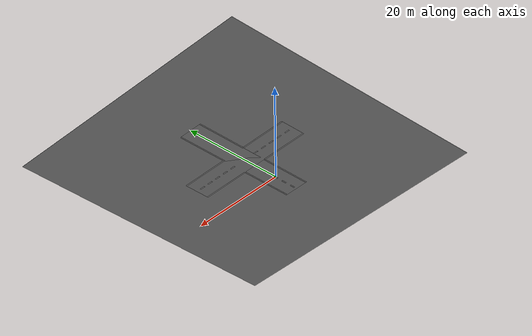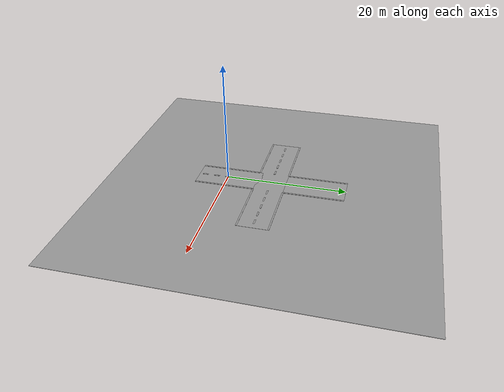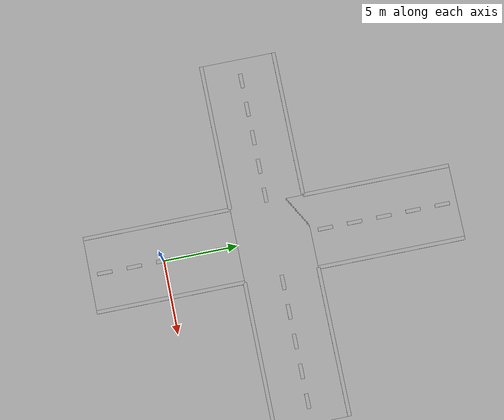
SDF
<?xml version='1.0'?>
<sdf version='1.7'>
  <model name='road_ground'>
    <link name='link_0'>
      <inertial>
        <mass>8812.5</mass>
        <inertia>
          <ixx>73454</ixx>
          <ixy>0</ixy>
          <ixz>0</ixz>
          <iyy>18375.9</iyy>
          <iyz>0</iyz>
          <izz>91796.9</izz>
        </inertia>
        <pose>0 0 0 0 -0 0</pose>
      </inertial>
      <pose>0 0 0 0 -0 0</pose>
      <gravity>1</gravity>
      <self_collide>0</self_collide>
      <kinematic>0</kinematic>
      <enable_wind>0</enable_wind>
      <visual name='ModelPreview_1::link_0::visual_5'>
        <pose>-2.5 15 0 0 -0 0</pose>
        <geometry>
          <box>
            <size>0.25 10 0.15</size>
          </box>
        </geometry>
        <material>
          <lighting>1</lighting>
          <script>
            <uri>file://media/materials/scripts/gazebo.material</uri>
            <name>Gazebo/Grey</name>
          </script>
          <shader type='pixel'>
            <normal_map>__default__</normal_map>
          </shader>
          <ambient>1 1 1 1</ambient>
          <diffuse>1 1 1 1</diffuse>
          <specular>1 1 1 1</specular>
          <emissive>1 1 1 1</emissive>
        </material>
        <transparency>0</transparency>
        <cast_shadows>1</cast_shadows>
      </visual>
      <visual name='ModelPreview_1::link_0::visual_4'>
        <pose>2.5 15 0 0 -0 0</pose>
        <geometry>
          <box>
            <size>0.25 10 0.15</size>
          </box>
        </geometry>
        <material>
          <lighting>1</lighting>
          <script>
            <uri>file://media/materials/scripts/gazebo.material</uri>
            <name>Gazebo/Grey</name>
          </script>
          <shader type='pixel'>
            <normal_map>__default__</normal_map>
          </shader>
          <ambient>1 1 1 1</ambient>
          <diffuse>1 1 1 1</diffuse>
          <specular>1 1 1 1</specular>
          <emissive>1 1 1 1</emissive>
        </material>
        <transparency>0</transparency>
        <cast_shadows>1</cast_shadows>
      </visual>
      <visual name='ModelPreview_1::link_0::visual_2'>
        <pose>0 7.5 0 0 -0 0</pose>
        <geometry>
          <box>
            <size>25 5 0.1</size>
          </box>
        </geometry>
        <material>
          <lighting>1</lighting>
          <script>
            <uri>file://media/materials/scripts/gazebo.material</uri>
            <name>Gazebo/Grey</name>
          </script>
          <shader type='pixel'>
            <normal_map>__default__</normal_map>
          </shader>
          <ambient>0.008 0.008 0.008 1</ambient>
          <diffuse>0.18 0.204 0.212 1</diffuse>
          <specular>0 0 0 1</specular>
          <emissive>0 0 0 1</emissive>
        </material>
        <transparency>0</transparency>
        <cast_shadows>1</cast_shadows>
      </visual>
      <visual name='ModelPreview_1::link_0::visual_10'>
        <pose>2.5 0 0 0 -0 0</pose>
        <geometry>
          <box>
            <size>0.25 10 0.15</size>
          </box>
        </geometry>
        <material>
          <lighting>1</lighting>
          <script>
            <uri>file://media/materials/scripts/gazebo.material</uri>
            <name>Gazebo/Grey</name>
          </script>
          <shader type='pixel'>
            <normal_map>__default__</normal_map>
          </shader>
          <ambient>1 1 1 1</ambient>
          <diffuse>1 1 1 1</diffuse>
          <specular>1 1 1 1</specular>
          <emissive>1 1 1 1</emissive>
        </material>
        <transparency>0</transparency>
        <cast_shadows>1</cast_shadows>
      </visual>
      <visual name='ModelPreview_32::link_0::visual_13'>
        <pose>-7.5 10 0 0 -0 0</pose>
        <geometry>
          <box>
            <size>10 0.25 0.15</size>
          </box>
        </geometry>
        <material>
          <lighting>1</lighting>
          <script>
            <uri>file://media/materials/scripts/gazebo.material</uri>
            <name>Gazebo/Grey</name>
          </script>
          <shader type='pixel'>
            <normal_map>__default__</normal_map>
          </shader>
          <ambient>1 1 1 1</ambient>
          <diffuse>1 1 1 1</diffuse>
          <specular>1 1 1 1</specular>
          <emissive>1 1 1 1</emissive>
        </material>
        <transparency>0</transparency>
        <cast_shadows>1</cast_shadows>
      </visual>
      <visual name='ModelPreview_1::link_0::visual_6'>
        <pose>-2.5 0 0 0 -0 0</pose>
        <geometry>
          <box>
            <size>0.25 10 0.15</size>
          </box>
        </geometry>
        <material>
          <lighting>1</lighting>
          <script>
            <uri>file://media/materials/scripts/gazebo.material</uri>
            <name>Gazebo/Grey</name>
          </script>
          <shader type='pixel'>
            <normal_map>__default__</normal_map>
          </shader>
          <ambient>1 1 1 1</ambient>
          <diffuse>1 1 1 1</diffuse>
          <specular>1 1 1 1</specular>
          <emissive>1 1 1 1</emissive>
        </material>
        <transparency>0</transparency>
        <cast_shadows>1</cast_shadows>
      </visual>
      <visual name='ModelPreview_29::link_0::visual_11'>
        <pose>0 7.5 0 0 -0 0</pose>
        <geometry>
          <box>
            <size>55 55 0.07</size>
          </box>
        </geometry>
        <material>
          <lighting>1</lighting>
          <script>
            <uri>file://media/materials/scripts/gazebo.material</uri>
            <name>Gazebo/Grey</name>
          </script>
          <shader type='pixel'>
            <normal_map>__default__</normal_map>
          </shader>
          <ambient>0.008 0.008 0.008 1</ambient>
          <diffuse>0.18 0.204 0.212 1</diffuse>
          <specular>0 0 0 1</specular>
          <emissive>0 0 0 1</emissive>
        </material>
        <transparency>0</transparency>
        <cast_shadows>1</cast_shadows>
      </visual>
      <visual name='ModelPreview_1::link_0::visual_7'>
        <pose>7.5 5 0 0 -0 0</pose>
        <geometry>
          <box>
            <size>10 0.25 0.15</size>
          </box>
        </geometry>
        <material>
          <lighting>1</lighting>
          <script>
            <uri>file://media/materials/scripts/gazebo.material</uri>
            <name>Gazebo/Grey</name>
          </script>
          <shader type='pixel'>
            <normal_map>__default__</normal_map>
          </shader>
          <ambient>1 1 1 1</ambient>
          <diffuse>1 1 1 1</diffuse>
          <specular>1 1 1 1</specular>
          <emissive>1 1 1 1</emissive>
        </material>
        <transparency>0</transparency>
        <cast_shadows>1</cast_shadows>
      </visual>
      <visual name='ModelPreview_1::link_0::visual_9'>
        <pose>-7.5 5 0 0 -0 0</pose>
        <geometry>
          <box>
            <size>10 0.25 0.15</size>
          </box>
        </geometry>
        <material>
          <lighting>1</lighting>
          <script>
            <uri>file://media/materials/scripts/gazebo.material</uri>
            <name>Gazebo/Grey</name>
          </script>
          <shader type='pixel'>
            <normal_map>__default__</normal_map>
          </shader>
          <ambient>1 1 1 1</ambient>
          <diffuse>1 1 1 1</diffuse>
          <specular>1 1 1 1</specular>
          <emissive>1 1 1 1</emissive>
        </material>
        <transparency>0</transparency>
        <cast_shadows>1</cast_shadows>
      </visual>
      <visual name='visual'>
        <pose>0 7.5 0 0 -0 0</pose>
        <geometry>
          <box>
            <size>5 25 0.1</size>
          </box>
        </geometry>
        <material>
          <lighting>1</lighting>
          <script>
            <uri>file://media/materials/scripts/gazebo.material</uri>
            <name>Gazebo/Grey</name>
          </script>
          <shader type='pixel'>
            <normal_map>__default__</normal_map>
          </shader>
          <ambient>0.008 0.008 0.008 1</ambient>
          <diffuse>0.18 0.204 0.212 1</diffuse>
          <specular>0 0 0 1</specular>
          <emissive>0 0 0 1</emissive>
        </material>
        <transparency>0</transparency>
        <cast_shadows>1</cast_shadows>
      </visual>
      <visual name='ModelPreview_1::link_0::visual_8'>
        <pose>7.5 10 0 0 -0 0</pose>
        <geometry>
          <box>
            <size>10 0.25 0.15</size>
          </box>
        </geometry>
        <material>
          <lighting>1</lighting>
          <script>
            <uri>file://media/materials/scripts/gazebo.material</uri>
            <name>Gazebo/Grey</name>
          </script>
          <shader type='pixel'>
            <normal_map>__default__</normal_map>
          </shader>
          <ambient>1 1 1 1</ambient>
          <diffuse>1 1 1 1</diffuse>
          <specular>1 1 1 1</specular>
          <emissive>1 1 1 1</emissive>
        </material>
        <transparency>0</transparency>
        <cast_shadows>1</cast_shadows>
      </visual>
      <visual name='ModelPreview_1::link_0::visual_3'>
        <pose>2.5 0 0 0 -0 0</pose>
        <geometry>
          <box>
            <size>0.25 10 0.15</size>
          </box>
        </geometry>
        <material>
          <lighting>1</lighting>
          <script>
            <uri>file://media/materials/scripts/gazebo.material</uri>
            <name>Gazebo/Grey</name>
          </script>
          <shader type='pixel'>
            <normal_map>__default__</normal_map>
          </shader>
          <ambient>1 1 1 1</ambient>
          <diffuse>1 1 1 1</diffuse>
          <specular>1 1 1 1</specular>
          <emissive>1 1 1 1</emissive>
        </material>
        <transparency>0</transparency>
        <cast_shadows>1</cast_shadows>
      </visual>
      <collision name='collision'>
        <laser_retro>0</laser_retro>
        <max_contacts>10</max_contacts>
        <pose>0 7.5 0 0 -0 0</pose>
        <geometry>
          <box>
            <size>5 25 0.15</size>
          </box>
        </geometry>
        <surface>
          <friction>
            <ode>
              <mu>1</mu>
              <mu2>1</mu2>
              <fdir1>0 0 0</fdir1>
              <slip1>0</slip1>
              <slip2>0</slip2>
            </ode>
            <torsional>
              <coefficient>1</coefficient>
              <patch_radius>0</patch_radius>
              <surface_radius>0</surface_radius>
              <use_patch_radius>1</use_patch_radius>
              <ode>
                <slip>0</slip>
              </ode>
            </torsional>
          </friction>
          <bounce>
            <restitution_coefficient>0</restitution_coefficient>
            <threshold>1e+06</threshold>
          </bounce>
          <contact>
            <collide_without_contact>0</collide_without_contact>
            <collide_without_contact_bitmask>1</collide_without_contact_bitmask>
            <collide_bitmask>1</collide_bitmask>
            <ode>
              <soft_cfm>0</soft_cfm>
              <soft_erp>0.2</soft_erp>
              <kp>1e+13</kp>
              <kd>1</kd>
              <max_vel>0.01</max_vel>
              <min_depth>0</min_depth>
            </ode>
            <bullet>
              <split_impulse>1</split_impulse>
              <split_impulse_penetration_threshold>-0.01</split_impulse_penetration_threshold>
              <soft_cfm>0</soft_cfm>
              <soft_erp>0.2</soft_erp>
              <kp>1e+13</kp>
              <kd>1</kd>
            </bullet>
          </contact>
        </surface>
      </collision>
      <collision name='collision_1'>
        <laser_retro>0</laser_retro>
        <max_contacts>10</max_contacts>
        <pose>0 7.5 0 0 -0 0</pose>
        <geometry>
          <box>
            <size>25 5 0.1</size>
          </box>
        </geometry>
        <surface>
          <friction>
            <ode>
              <mu>1</mu>
              <mu2>1</mu2>
              <fdir1>0 0 0</fdir1>
              <slip1>0</slip1>
              <slip2>0</slip2>
            </ode>
            <torsional>
              <coefficient>1</coefficient>
              <patch_radius>0</patch_radius>
              <surface_radius>0</surface_radius>
              <use_patch_radius>1</use_patch_radius>
              <ode>
                <slip>0</slip>
              </ode>
            </torsional>
          </friction>
          <bounce>
            <restitution_coefficient>0</restitution_coefficient>
            <threshold>1e+06</threshold>
          </bounce>
          <contact>
            <collide_without_contact>0</collide_without_contact>
            <collide_without_contact_bitmask>1</collide_without_contact_bitmask>
            <collide_bitmask>1</collide_bitmask>
            <ode>
              <soft_cfm>0</soft_cfm>
              <soft_erp>0.2</soft_erp>
              <kp>1e+13</kp>
              <kd>1</kd>
              <max_vel>0.01</max_vel>
              <min_depth>0</min_depth>
            </ode>
            <bullet>
              <split_impulse>1</split_impulse>
              <split_impulse_penetration_threshold>-0.01</split_impulse_penetration_threshold>
              <soft_cfm>0</soft_cfm>
              <soft_erp>0.2</soft_erp>
              <kp>1e+13</kp>
              <kd>1</kd>
            </bullet>
          </contact>
        </surface>
      </collision>
    </link>
    <link name='link_1_clone'>
      <inertial>
        <mass>44.0625</mass>
        <inertia>
          <ixx>3.75449</ixx>
          <ixy>0</ixy>
          <ixz>0</ixz>
          <iyy>0.312109</iyy>
          <iyz>0</iyz>
          <izz>3.90137</izz>
        </inertia>
        <pose>0 0 0 0 -0 0</pose>
      </inertial>
      <pose>0 2 0 0 -0 0</pose>
      <gravity>1</gravity>
      <self_collide>0</self_collide>
      <kinematic>0</kinematic>
      <enable_wind>0</enable_wind>
      <visual name='visual'>
        <pose>0 0 0 0 -0 0</pose>
        <geometry>
          <box>
            <size>0.25 1 0.15</size>
          </box>
        </geometry>
        <material>
          <lighting>1</lighting>
          <script>
            <uri>file://media/materials/scripts/gazebo.material</uri>
            <name>Gazebo/Grey</name>
          </script>
          <shader type='normal_map_object_space'>
            <normal_map>__default__</normal_map>
          </shader>
          <ambient>1 1 1 1</ambient>
          <diffuse>1 1 1 1</diffuse>
          <specular>1 1 1 1</specular>
          <emissive>0 0 0 1</emissive>
        </material>
        <transparency>0</transparency>
        <cast_shadows>1</cast_shadows>
      </visual>
      <collision name='collision_1'>
        <laser_retro>0</laser_retro>
        <max_contacts>10</max_contacts>
        <pose>0 0 0 0 -0 0</pose>
        <geometry>
          <box>
            <size>0.25 1 0.2</size>
          </box>
        </geometry>
        <surface>
          <friction>
            <ode>
              <mu>1</mu>
              <mu2>1</mu2>
              <fdir1>0 0 0</fdir1>
              <slip1>0</slip1>
              <slip2>0</slip2>
            </ode>
            <torsional>
              <coefficient>1</coefficient>
              <patch_radius>0</patch_radius>
              <surface_radius>0</surface_radius>
              <use_patch_radius>1</use_patch_radius>
              <ode>
                <slip>0</slip>
              </ode>
            </torsional>
          </friction>
          <bounce>
            <restitution_coefficient>0</restitution_coefficient>
            <threshold>1e+06</threshold>
          </bounce>
          <contact>
            <collide_without_contact>0</collide_without_contact>
            <collide_without_contact_bitmask>1</collide_without_contact_bitmask>
            <collide_bitmask>1</collide_bitmask>
            <ode>
              <soft_cfm>0</soft_cfm>
              <soft_erp>0.2</soft_erp>
              <kp>1e+13</kp>
              <kd>1</kd>
              <max_vel>0.01</max_vel>
              <min_depth>0</min_depth>
            </ode>
            <bullet>
              <split_impulse>1</split_impulse>
              <split_impulse_penetration_threshold>-0.01</split_impulse_penetration_threshold>
              <soft_cfm>0</soft_cfm>
              <soft_erp>0.2</soft_erp>
              <kp>1e+13</kp>
              <kd>1</kd>
            </bullet>
          </contact>
        </surface>
      </collision>
    </link>
    <link name='link_1_clone_0'>
      <inertial>
        <mass>44.0625</mass>
        <inertia>
          <ixx>3.75449</ixx>
          <ixy>0</ixy>
          <ixz>0</ixz>
          <iyy>0.312109</iyy>
          <iyz>0</iyz>
          <izz>3.90137</izz>
        </inertia>
        <pose>0 0 0 0 -0 0</pose>
      </inertial>
      <pose>0 0 0 0 -0 0</pose>
      <gravity>1</gravity>
      <self_collide>0</self_collide>
      <kinematic>0</kinematic>
      <enable_wind>0</enable_wind>
      <visual name='visual'>
        <pose>0 0 0 0 -0 0</pose>
        <geometry>
          <box>
            <size>0.25 1 0.15</size>
          </box>
        </geometry>
        <material>
          <lighting>1</lighting>
          <script>
            <uri>file://media/materials/scripts/gazebo.material</uri>
            <name>Gazebo/Grey</name>
          </script>
          <shader type='normal_map_object_space'>
            <normal_map>__default__</normal_map>
          </shader>
          <ambient>1 1 1 1</ambient>
          <diffuse>1 1 1 1</diffuse>
          <specular>1 1 1 1</specular>
          <emissive>0 0 0 1</emissive>
        </material>
        <transparency>0</transparency>
        <cast_shadows>1</cast_shadows>
      </visual>
      <collision name='collision_1'>
        <laser_retro>0</laser_retro>
        <max_contacts>10</max_contacts>
        <pose>0 0 0 0 -0 0</pose>
        <geometry>
          <box>
            <size>0.25 1 0.2</size>
          </box>
        </geometry>
        <surface>
          <friction>
            <ode>
              <mu>1</mu>
              <mu2>1</mu2>
              <fdir1>0 0 0</fdir1>
              <slip1>0</slip1>
              <slip2>0</slip2>
            </ode>
            <torsional>
              <coefficient>1</coefficient>
              <patch_radius>0</patch_radius>
              <surface_radius>0</surface_radius>
              <use_patch_radius>1</use_patch_radius>
              <ode>
                <slip>0</slip>
              </ode>
            </torsional>
          </friction>
          <bounce>
            <restitution_coefficient>0</restitution_coefficient>
            <threshold>1e+06</threshold>
          </bounce>
          <contact>
            <collide_without_contact>0</collide_without_contact>
            <collide_without_contact_bitmask>1</collide_without_contact_bitmask>
            <collide_bitmask>1</collide_bitmask>
            <ode>
              <soft_cfm>0</soft_cfm>
              <soft_erp>0.2</soft_erp>
              <kp>1e+13</kp>
              <kd>1</kd>
              <max_vel>0.01</max_vel>
              <min_depth>0</min_depth>
            </ode>
            <bullet>
              <split_impulse>1</split_impulse>
              <split_impulse_penetration_threshold>-0.01</split_impulse_penetration_threshold>
              <soft_cfm>0</soft_cfm>
              <soft_erp>0.2</soft_erp>
              <kp>1e+13</kp>
              <kd>1</kd>
            </bullet>
          </contact>
        </surface>
      </collision>
    </link>
    <link name='link_1_clone_1'>
      <inertial>
        <mass>44.0625</mass>
        <inertia>
          <ixx>3.75449</ixx>
          <ixy>0</ixy>
          <ixz>0</ixz>
          <iyy>0.312109</iyy>
          <iyz>0</iyz>
          <izz>3.90137</izz>
        </inertia>
        <pose>0 0 0 0 -0 0</pose>
      </inertial>
      <pose>0 -2 0 0 -0 0</pose>
      <gravity>1</gravity>
      <self_collide>0</self_collide>
      <kinematic>0</kinematic>
      <enable_wind>0</enable_wind>
      <visual name='visual'>
        <pose>0 0 0 0 -0 0</pose>
        <geometry>
          <box>
            <size>0.25 1 0.15</size>
          </box>
        </geometry>
        <material>
          <lighting>1</lighting>
          <script>
            <uri>file://media/materials/scripts/gazebo.material</uri>
            <name>Gazebo/Grey</name>
          </script>
          <shader type='normal_map_object_space'>
            <normal_map>__default__</normal_map>
          </shader>
          <ambient>1 1 1 1</ambient>
          <diffuse>1 1 1 1</diffuse>
          <specular>1 1 1 1</specular>
          <emissive>0 0 0 1</emissive>
        </material>
        <transparency>0</transparency>
        <cast_shadows>1</cast_shadows>
      </visual>
      <collision name='collision_1'>
        <laser_retro>0</laser_retro>
        <max_contacts>10</max_contacts>
        <pose>0 0 0 0 -0 0</pose>
        <geometry>
          <box>
            <size>0.25 1 0.2</size>
          </box>
        </geometry>
        <surface>
          <friction>
            <ode>
              <mu>1</mu>
              <mu2>1</mu2>
              <fdir1>0 0 0</fdir1>
              <slip1>0</slip1>
              <slip2>0</slip2>
            </ode>
            <torsional>
              <coefficient>1</coefficient>
              <patch_radius>0</patch_radius>
              <surface_radius>0</surface_radius>
              <use_patch_radius>1</use_patch_radius>
              <ode>
                <slip>0</slip>
              </ode>
            </torsional>
          </friction>
          <bounce>
            <restitution_coefficient>0</restitution_coefficient>
            <threshold>1e+06</threshold>
          </bounce>
          <contact>
            <collide_without_contact>0</collide_without_contact>
            <collide_without_contact_bitmask>1</collide_without_contact_bitmask>
            <collide_bitmask>1</collide_bitmask>
            <ode>
              <soft_cfm>0</soft_cfm>
              <soft_erp>0.2</soft_erp>
              <kp>1e+13</kp>
              <kd>1</kd>
              <max_vel>0.01</max_vel>
              <min_depth>0</min_depth>
            </ode>
            <bullet>
              <split_impulse>1</split_impulse>
              <split_impulse_penetration_threshold>-0.01</split_impulse_penetration_threshold>
              <soft_cfm>0</soft_cfm>
              <soft_erp>0.2</soft_erp>
              <kp>1e+13</kp>
              <kd>1</kd>
            </bullet>
          </contact>
        </surface>
      </collision>
    </link>
    <link name='link_1_clone_2'>
      <inertial>
        <mass>44.0625</mass>
        <inertia>
          <ixx>3.75449</ixx>
          <ixy>0</ixy>
          <ixz>0</ixz>
          <iyy>0.312109</iyy>
          <iyz>0</iyz>
          <izz>3.90137</izz>
        </inertia>
        <pose>0 0 0 0 -0 0</pose>
      </inertial>
      <pose>0 4 0 0 -0 0</pose>
      <gravity>1</gravity>
      <self_collide>0</self_collide>
      <kinematic>0</kinematic>
      <enable_wind>0</enable_wind>
      <visual name='visual'>
        <pose>0 0 0 0 -0 0</pose>
        <geometry>
          <box>
            <size>0.25 1 0.15</size>
          </box>
        </geometry>
        <material>
          <lighting>1</lighting>
          <script>
            <uri>file://media/materials/scripts/gazebo.material</uri>
            <name>Gazebo/Grey</name>
          </script>
          <shader type='normal_map_object_space'>
            <normal_map>__default__</normal_map>
          </shader>
          <ambient>1 1 1 1</ambient>
          <diffuse>1 1 1 1</diffuse>
          <specular>1 1 1 1</specular>
          <emissive>0 0 0 1</emissive>
        </material>
        <transparency>0</transparency>
        <cast_shadows>1</cast_shadows>
      </visual>
      <collision name='collision_1'>
        <laser_retro>0</laser_retro>
        <max_contacts>10</max_contacts>
        <pose>0 0 0 0 -0 0</pose>
        <geometry>
          <box>
            <size>0.25 1 0.2</size>
          </box>
        </geometry>
        <surface>
          <friction>
            <ode>
              <mu>1</mu>
              <mu2>1</mu2>
              <fdir1>0 0 0</fdir1>
              <slip1>0</slip1>
              <slip2>0</slip2>
            </ode>
            <torsional>
              <coefficient>1</coefficient>
              <patch_radius>0</patch_radius>
              <surface_radius>0</surface_radius>
              <use_patch_radius>1</use_patch_radius>
              <ode>
                <slip>0</slip>
              </ode>
            </torsional>
          </friction>
          <bounce>
            <restitution_coefficient>0</restitution_coefficient>
            <threshold>1e+06</threshold>
          </bounce>
          <contact>
            <collide_without_contact>0</collide_without_contact>
            <collide_without_contact_bitmask>1</collide_without_contact_bitmask>
            <collide_bitmask>1</collide_bitmask>
            <ode>
              <soft_cfm>0</soft_cfm>
              <soft_erp>0.2</soft_erp>
              <kp>1e+13</kp>
              <kd>1</kd>
              <max_vel>0.01</max_vel>
              <min_depth>0</min_depth>
            </ode>
            <bullet>
              <split_impulse>1</split_impulse>
              <split_impulse_penetration_threshold>-0.01</split_impulse_penetration_threshold>
              <soft_cfm>0</soft_cfm>
              <soft_erp>0.2</soft_erp>
              <kp>1e+13</kp>
              <kd>1</kd>
            </bullet>
          </contact>
        </surface>
      </collision>
    </link>
    <link name='link_1_clone_2_clone'>
      <inertial>
        <mass>44.0625</mass>
        <inertia>
          <ixx>3.75449</ixx>
          <ixy>0</ixy>
          <ixz>0</ixz>
          <iyy>0.312109</iyy>
          <iyz>0</iyz>
          <izz>3.90137</izz>
        </inertia>
        <pose>0 0 0 0 -0 0</pose>
      </inertial>
      <pose>0 11 0 0 -0 0</pose>
      <gravity>1</gravity>
      <self_collide>0</self_collide>
      <kinematic>0</kinematic>
      <enable_wind>0</enable_wind>
      <visual name='visual'>
        <pose>0 0 0 0 -0 0</pose>
        <geometry>
          <box>
            <size>0.25 1 0.15</size>
          </box>
        </geometry>
        <material>
          <lighting>1</lighting>
          <script>
            <uri>file://media/materials/scripts/gazebo.material</uri>
            <name>Gazebo/Grey</name>
          </script>
          <shader type='normal_map_object_space'>
            <normal_map>__default__</normal_map>
          </shader>
          <ambient>1 1 1 1</ambient>
          <diffuse>1 1 1 1</diffuse>
          <specular>1 1 1 1</specular>
          <emissive>0 0 0 1</emissive>
        </material>
        <transparency>0</transparency>
        <cast_shadows>1</cast_shadows>
      </visual>
      <collision name='collision_1'>
        <laser_retro>0</laser_retro>
        <max_contacts>10</max_contacts>
        <pose>0 0 0 0 -0 0</pose>
        <geometry>
          <box>
            <size>0.25 1 0.2</size>
          </box>
        </geometry>
        <surface>
          <friction>
            <ode>
              <mu>1</mu>
              <mu2>1</mu2>
              <fdir1>0 0 0</fdir1>
              <slip1>0</slip1>
              <slip2>0</slip2>
            </ode>
            <torsional>
              <coefficient>1</coefficient>
              <patch_radius>0</patch_radius>
              <surface_radius>0</surface_radius>
              <use_patch_radius>1</use_patch_radius>
              <ode>
                <slip>0</slip>
              </ode>
            </torsional>
          </friction>
          <bounce>
            <restitution_coefficient>0</restitution_coefficient>
            <threshold>1e+06</threshold>
          </bounce>
          <contact>
            <collide_without_contact>0</collide_without_contact>
            <collide_without_contact_bitmask>1</collide_without_contact_bitmask>
            <collide_bitmask>1</collide_bitmask>
            <ode>
              <soft_cfm>0</soft_cfm>
              <soft_erp>0.2</soft_erp>
              <kp>1e+13</kp>
              <kd>1</kd>
              <max_vel>0.01</max_vel>
              <min_depth>0</min_depth>
            </ode>
            <bullet>
              <split_impulse>1</split_impulse>
              <split_impulse_penetration_threshold>-0.01</split_impulse_penetration_threshold>
              <soft_cfm>0</soft_cfm>
              <soft_erp>0.2</soft_erp>
              <kp>1e+13</kp>
              <kd>1</kd>
            </bullet>
          </contact>
        </surface>
      </collision>
    </link>
    <link name='link_1_clone_2_clone_0'>
      <inertial>
        <mass>44.0625</mass>
        <inertia>
          <ixx>3.75449</ixx>
          <ixy>0</ixy>
          <ixz>0</ixz>
          <iyy>0.312109</iyy>
          <iyz>0</iyz>
          <izz>3.90137</izz>
        </inertia>
        <pose>0 0 0 0 -0 0</pose>
      </inertial>
      <pose>-3 7.5 0 0 -0 0</pose>
      <gravity>1</gravity>
      <self_collide>0</self_collide>
      <kinematic>0</kinematic>
      <enable_wind>0</enable_wind>
      <visual name='visual'>
        <pose>0 0 0 0 -0 0</pose>
        <geometry>
          <box>
            <size>1 0.25 0.15</size>
          </box>
        </geometry>
        <material>
          <lighting>1</lighting>
          <script>
            <uri>file://media/materials/scripts/gazebo.material</uri>
            <name>Gazebo/Grey</name>
          </script>
          <shader type='normal_map_object_space'>
            <normal_map>__default__</normal_map>
          </shader>
          <ambient>1 1 1 1</ambient>
          <diffuse>1 1 1 1</diffuse>
          <specular>1 1 1 1</specular>
          <emissive>0 0 0 1</emissive>
        </material>
        <transparency>0</transparency>
        <cast_shadows>1</cast_shadows>
      </visual>
      <collision name='collision_1'>
        <laser_retro>0</laser_retro>
        <max_contacts>10</max_contacts>
        <pose>0 0 0 0 -0 0</pose>
        <geometry>
          <box>
            <size>1 0.25 0.2</size>
          </box>
        </geometry>
        <surface>
          <friction>
            <ode>
              <mu>1</mu>
              <mu2>1</mu2>
              <fdir1>0 0 0</fdir1>
              <slip1>0</slip1>
              <slip2>0</slip2>
            </ode>
            <torsional>
              <coefficient>1</coefficient>
              <patch_radius>0</patch_radius>
              <surface_radius>0</surface_radius>
              <use_patch_radius>1</use_patch_radius>
              <ode>
                <slip>0</slip>
              </ode>
            </torsional>
          </friction>
          <bounce>
            <restitution_coefficient>0</restitution_coefficient>
            <threshold>1e+06</threshold>
          </bounce>
          <contact>
            <collide_without_contact>0</collide_without_contact>
            <collide_without_contact_bitmask>1</collide_without_contact_bitmask>
            <collide_bitmask>1</collide_bitmask>
            <ode>
              <soft_cfm>0</soft_cfm>
              <soft_erp>0.2</soft_erp>
              <kp>1e+13</kp>
              <kd>1</kd>
              <max_vel>0.01</max_vel>
              <min_depth>0</min_depth>
            </ode>
            <bullet>
              <split_impulse>1</split_impulse>
              <split_impulse_penetration_threshold>-0.01</split_impulse_penetration_threshold>
              <soft_cfm>0</soft_cfm>
              <soft_erp>0.2</soft_erp>
              <kp>1e+13</kp>
              <kd>1</kd>
            </bullet>
          </contact>
        </surface>
      </collision>
    </link>
    <link name='link_1_clone_2_clone_0_clone'>
      <inertial>
        <mass>44.0625</mass>
        <inertia>
          <ixx>3.75449</ixx>
          <ixy>0</ixy>
          <ixz>0</ixz>
          <iyy>0.312109</iyy>
          <iyz>0</iyz>
          <izz>3.90137</izz>
        </inertia>
        <pose>0 0 0 0 -0 0</pose>
      </inertial>
      <pose>-5 7.5 0 0 -0 0</pose>
      <gravity>1</gravity>
      <self_collide>0</self_collide>
      <kinematic>0</kinematic>
      <enable_wind>0</enable_wind>
      <visual name='visual'>
        <pose>0 0 0 0 -0 0</pose>
        <geometry>
          <box>
            <size>1 0.25 0.15</size>
          </box>
        </geometry>
        <material>
          <lighting>1</lighting>
          <script>
            <uri>file://media/materials/scripts/gazebo.material</uri>
            <name>Gazebo/Grey</name>
          </script>
          <shader type='normal_map_object_space'>
            <normal_map>__default__</normal_map>
          </shader>
          <ambient>1 1 1 1</ambient>
          <diffuse>1 1 1 1</diffuse>
          <specular>1 1 1 1</specular>
          <emissive>0 0 0 1</emissive>
        </material>
        <transparency>0</transparency>
        <cast_shadows>1</cast_shadows>
      </visual>
      <collision name='collision_1'>
        <laser_retro>0</laser_retro>
        <max_contacts>10</max_contacts>
        <pose>0 0 0 0 -0 0</pose>
        <geometry>
          <box>
            <size>1 0.25 0.2</size>
          </box>
        </geometry>
        <surface>
          <friction>
            <ode>
              <mu>1</mu>
              <mu2>1</mu2>
              <fdir1>0 0 0</fdir1>
              <slip1>0</slip1>
              <slip2>0</slip2>
            </ode>
            <torsional>
              <coefficient>1</coefficient>
              <patch_radius>0</patch_radius>
              <surface_radius>0</surface_radius>
              <use_patch_radius>1</use_patch_radius>
              <ode>
                <slip>0</slip>
              </ode>
            </torsional>
          </friction>
          <bounce>
            <restitution_coefficient>0</restitution_coefficient>
            <threshold>1e+06</threshold>
          </bounce>
          <contact>
            <collide_without_contact>0</collide_without_contact>
            <collide_without_contact_bitmask>1</collide_without_contact_bitmask>
            <collide_bitmask>1</collide_bitmask>
            <ode>
              <soft_cfm>0</soft_cfm>
              <soft_erp>0.2</soft_erp>
              <kp>1e+13</kp>
              <kd>1</kd>
              <max_vel>0.01</max_vel>
              <min_depth>0</min_depth>
            </ode>
            <bullet>
              <split_impulse>1</split_impulse>
              <split_impulse_penetration_threshold>-0.01</split_impulse_penetration_threshold>
              <soft_cfm>0</soft_cfm>
              <soft_erp>0.2</soft_erp>
              <kp>1e+13</kp>
              <kd>1</kd>
            </bullet>
          </contact>
        </surface>
      </collision>
    </link>
    <link name='link_1_clone_2_clone_0_clone_0'>
      <inertial>
        <mass>44.0625</mass>
        <inertia>
          <ixx>3.75449</ixx>
          <ixy>0</ixy>
          <ixz>0</ixz>
          <iyy>0.312109</iyy>
          <iyz>0</iyz>
          <izz>3.90137</izz>
        </inertia>
        <pose>0 0 0 0 -0 0</pose>
      </inertial>
      <pose>-7 7.5 0 0 -0 0</pose>
      <gravity>1</gravity>
      <self_collide>0</self_collide>
      <kinematic>0</kinematic>
      <enable_wind>0</enable_wind>
      <visual name='visual'>
        <pose>0 0 0 0 -0 0</pose>
        <geometry>
          <box>
            <size>1 0.25 0.15</size>
          </box>
        </geometry>
        <material>
          <lighting>1</lighting>
          <script>
            <uri>file://media/materials/scripts/gazebo.material</uri>
            <name>Gazebo/Grey</name>
          </script>
          <shader type='normal_map_object_space'>
            <normal_map>__default__</normal_map>
          </shader>
          <ambient>1 1 1 1</ambient>
          <diffuse>1 1 1 1</diffuse>
          <specular>1 1 1 1</specular>
          <emissive>0 0 0 1</emissive>
        </material>
        <transparency>0</transparency>
        <cast_shadows>1</cast_shadows>
      </visual>
      <collision name='collision_1'>
        <laser_retro>0</laser_retro>
        <max_contacts>10</max_contacts>
        <pose>0 0 0 0 -0 0</pose>
        <geometry>
          <box>
            <size>1 0.25 0.2</size>
          </box>
        </geometry>
        <surface>
          <friction>
            <ode>
              <mu>1</mu>
              <mu2>1</mu2>
              <fdir1>0 0 0</fdir1>
              <slip1>0</slip1>
              <slip2>0</slip2>
            </ode>
            <torsional>
              <coefficient>1</coefficient>
              <patch_radius>0</patch_radius>
              <surface_radius>0</surface_radius>
              <use_patch_radius>1</use_patch_radius>
              <ode>
                <slip>0</slip>
              </ode>
            </torsional>
          </friction>
          <bounce>
            <restitution_coefficient>0</restitution_coefficient>
            <threshold>1e+06</threshold>
          </bounce>
          <contact>
            <collide_without_contact>0</collide_without_contact>
            <collide_without_contact_bitmask>1</collide_without_contact_bitmask>
            <collide_bitmask>1</collide_bitmask>
            <ode>
              <soft_cfm>0</soft_cfm>
              <soft_erp>0.2</soft_erp>
              <kp>1e+13</kp>
              <kd>1</kd>
              <max_vel>0.01</max_vel>
              <min_depth>0</min_depth>
            </ode>
            <bullet>
              <split_impulse>1</split_impulse>
              <split_impulse_penetration_threshold>-0.01</split_impulse_penetration_threshold>
              <soft_cfm>0</soft_cfm>
              <soft_erp>0.2</soft_erp>
              <kp>1e+13</kp>
              <kd>1</kd>
            </bullet>
          </contact>
        </surface>
      </collision>
    </link>
    <link name='link_1_clone_2_clone_0_clone_1'>
      <inertial>
        <mass>44.0625</mass>
        <inertia>
          <ixx>3.75449</ixx>
          <ixy>0</ixy>
          <ixz>0</ixz>
          <iyy>0.312109</iyy>
          <iyz>0</iyz>
          <izz>3.90137</izz>
        </inertia>
        <pose>0 0 0 0 -0 0</pose>
      </inertial>
      <pose>-9 7.5 0 0 -0 0</pose>
      <gravity>1</gravity>
      <self_collide>0</self_collide>
      <kinematic>0</kinematic>
      <enable_wind>0</enable_wind>
      <visual name='visual'>
        <pose>0 0 0 0 -0 0</pose>
        <geometry>
          <box>
            <size>1 0.25 0.15</size>
          </box>
        </geometry>
        <material>
          <lighting>1</lighting>
          <script>
            <uri>file://media/materials/scripts/gazebo.material</uri>
            <name>Gazebo/Grey</name>
          </script>
          <shader type='normal_map_object_space'>
            <normal_map>__default__</normal_map>
          </shader>
          <ambient>1 1 1 1</ambient>
          <diffuse>1 1 1 1</diffuse>
          <specular>1 1 1 1</specular>
          <emissive>0 0 0 1</emissive>
        </material>
        <transparency>0</transparency>
        <cast_shadows>1</cast_shadows>
      </visual>
      <collision name='collision_1'>
        <laser_retro>0</laser_retro>
        <max_contacts>10</max_contacts>
        <pose>0 0 0 0 -0 0</pose>
        <geometry>
          <box>
            <size>1 0.25 0.2</size>
          </box>
        </geometry>
        <surface>
          <friction>
            <ode>
              <mu>1</mu>
              <mu2>1</mu2>
              <fdir1>0 0 0</fdir1>
              <slip1>0</slip1>
              <slip2>0</slip2>
            </ode>
            <torsional>
              <coefficient>1</coefficient>
              <patch_radius>0</patch_radius>
              <surface_radius>0</surface_radius>
              <use_patch_radius>1</use_patch_radius>
              <ode>
                <slip>0</slip>
              </ode>
            </torsional>
          </friction>
          <bounce>
            <restitution_coefficient>0</restitution_coefficient>
            <threshold>1e+06</threshold>
          </bounce>
          <contact>
            <collide_without_contact>0</collide_without_contact>
            <collide_without_contact_bitmask>1</collide_without_contact_bitmask>
            <collide_bitmask>1</collide_bitmask>
            <ode>
              <soft_cfm>0</soft_cfm>
              <soft_erp>0.2</soft_erp>
              <kp>1e+13</kp>
              <kd>1</kd>
              <max_vel>0.01</max_vel>
              <min_depth>0</min_depth>
            </ode>
            <bullet>
              <split_impulse>1</split_impulse>
              <split_impulse_penetration_threshold>-0.01</split_impulse_penetration_threshold>
              <soft_cfm>0</soft_cfm>
              <soft_erp>0.2</soft_erp>
              <kp>1e+13</kp>
              <kd>1</kd>
            </bullet>
          </contact>
        </surface>
      </collision>
    </link>
    <link name='link_1_clone_2_clone_0_clone_1_clone'>
      <inertial>
        <mass>44.0625</mass>
        <inertia>
          <ixx>3.75449</ixx>
          <ixy>0</ixy>
          <ixz>0</ixz>
          <iyy>0.312109</iyy>
          <iyz>0</iyz>
          <izz>3.90137</izz>
        </inertia>
        <pose>0 0 0 0 -0 0</pose>
      </inertial>
      <pose>-11 7.5 0 0 -0 0</pose>
      <gravity>1</gravity>
      <self_collide>0</self_collide>
      <kinematic>0</kinematic>
      <enable_wind>0</enable_wind>
      <visual name='visual'>
        <pose>0 0 0 0 -0 0</pose>
        <geometry>
          <box>
            <size>1 0.25 0.15</size>
          </box>
        </geometry>
        <material>
          <lighting>1</lighting>
          <script>
            <uri>file://media/materials/scripts/gazebo.material</uri>
            <name>Gazebo/Grey</name>
          </script>
          <shader type='normal_map_object_space'>
            <normal_map>__default__</normal_map>
          </shader>
          <ambient>1 1 1 1</ambient>
          <diffuse>1 1 1 1</diffuse>
          <specular>1 1 1 1</specular>
          <emissive>0 0 0 1</emissive>
        </material>
        <transparency>0</transparency>
        <cast_shadows>1</cast_shadows>
      </visual>
      <collision name='collision_1'>
        <laser_retro>0</laser_retro>
        <max_contacts>10</max_contacts>
        <pose>0 0 0 0 -0 0</pose>
        <geometry>
          <box>
            <size>1 0.25 0.2</size>
          </box>
        </geometry>
        <surface>
          <friction>
            <ode>
              <mu>1</mu>
              <mu2>1</mu2>
              <fdir1>0 0 0</fdir1>
              <slip1>0</slip1>
              <slip2>0</slip2>
            </ode>
            <torsional>
              <coefficient>1</coefficient>
              <patch_radius>0</patch_radius>
              <surface_radius>0</surface_radius>
              <use_patch_radius>1</use_patch_radius>
              <ode>
                <slip>0</slip>
              </ode>
            </torsional>
          </friction>
          <bounce>
            <restitution_coefficient>0</restitution_coefficient>
            <threshold>1e+06</threshold>
          </bounce>
          <contact>
            <collide_without_contact>0</collide_without_contact>
            <collide_without_contact_bitmask>1</collide_without_contact_bitmask>
            <collide_bitmask>1</collide_bitmask>
            <ode>
              <soft_cfm>0</soft_cfm>
              <soft_erp>0.2</soft_erp>
              <kp>1e+13</kp>
              <kd>1</kd>
              <max_vel>0.01</max_vel>
              <min_depth>0</min_depth>
            </ode>
            <bullet>
              <split_impulse>1</split_impulse>
              <split_impulse_penetration_threshold>-0.01</split_impulse_penetration_threshold>
              <soft_cfm>0</soft_cfm>
              <soft_erp>0.2</soft_erp>
              <kp>1e+13</kp>
              <kd>1</kd>
            </bullet>
          </contact>
        </surface>
      </collision>
    </link>
    <link name='link_1_clone_2_clone_0_clone_1_clone_0'>
      <inertial>
        <mass>44.0625</mass>
        <inertia>
          <ixx>3.75449</ixx>
          <ixy>0</ixy>
          <ixz>0</ixz>
          <iyy>0.312109</iyy>
          <iyz>0</iyz>
          <izz>3.90137</izz>
        </inertia>
        <pose>0 0 0 0 -0 0</pose>
      </inertial>
      <pose>11 7.5 0 0 -0 0</pose>
      <gravity>1</gravity>
      <self_collide>0</self_collide>
      <kinematic>0</kinematic>
      <enable_wind>0</enable_wind>
      <visual name='visual'>
        <pose>0 0 0 0 -0 0</pose>
        <geometry>
          <box>
            <size>1 0.25 0.15</size>
          </box>
        </geometry>
        <material>
          <lighting>1</lighting>
          <script>
            <uri>file://media/materials/scripts/gazebo.material</uri>
            <name>Gazebo/Grey</name>
          </script>
          <shader type='normal_map_object_space'>
            <normal_map>__default__</normal_map>
          </shader>
          <ambient>1 1 1 1</ambient>
          <diffuse>1 1 1 1</diffuse>
          <specular>1 1 1 1</specular>
          <emissive>0 0 0 1</emissive>
        </material>
        <transparency>0</transparency>
        <cast_shadows>1</cast_shadows>
      </visual>
      <collision name='collision_1'>
        <laser_retro>0</laser_retro>
        <max_contacts>10</max_contacts>
        <pose>0 0 0 0 -0 0</pose>
        <geometry>
          <box>
            <size>1 0.25 0.2</size>
          </box>
        </geometry>
        <surface>
          <friction>
            <ode>
              <mu>1</mu>
              <mu2>1</mu2>
              <fdir1>0 0 0</fdir1>
              <slip1>0</slip1>
              <slip2>0</slip2>
            </ode>
            <torsional>
              <coefficient>1</coefficient>
              <patch_radius>0</patch_radius>
              <surface_radius>0</surface_radius>
              <use_patch_radius>1</use_patch_radius>
              <ode>
                <slip>0</slip>
              </ode>
            </torsional>
          </friction>
          <bounce>
            <restitution_coefficient>0</restitution_coefficient>
            <threshold>1e+06</threshold>
          </bounce>
          <contact>
            <collide_without_contact>0</collide_without_contact>
            <collide_without_contact_bitmask>1</collide_without_contact_bitmask>
            <collide_bitmask>1</collide_bitmask>
            <ode>
              <soft_cfm>0</soft_cfm>
              <soft_erp>0.2</soft_erp>
              <kp>1e+13</kp>
              <kd>1</kd>
              <max_vel>0.01</max_vel>
              <min_depth>0</min_depth>
            </ode>
            <bullet>
              <split_impulse>1</split_impulse>
              <split_impulse_penetration_threshold>-0.01</split_impulse_penetration_threshold>
              <soft_cfm>0</soft_cfm>
              <soft_erp>0.2</soft_erp>
              <kp>1e+13</kp>
              <kd>1</kd>
            </bullet>
          </contact>
        </surface>
      </collision>
    </link>
    <link name='link_1_clone_2_clone_0_clone_2'>
      <inertial>
        <mass>44.0625</mass>
        <inertia>
          <ixx>3.75449</ixx>
          <ixy>0</ixy>
          <ixz>0</ixz>
          <iyy>0.312109</iyy>
          <iyz>0</iyz>
          <izz>3.90137</izz>
        </inertia>
        <pose>0 0 0 0 -0 0</pose>
      </inertial>
      <pose>3 7.5 0 0 -0 0</pose>
      <gravity>1</gravity>
      <self_collide>0</self_collide>
      <kinematic>0</kinematic>
      <enable_wind>0</enable_wind>
      <visual name='visual'>
        <pose>0 0 0 0 -0 0</pose>
        <geometry>
          <box>
            <size>1 0.25 0.15</size>
          </box>
        </geometry>
        <material>
          <lighting>1</lighting>
          <script>
            <uri>file://media/materials/scripts/gazebo.material</uri>
            <name>Gazebo/Grey</name>
          </script>
          <shader type='normal_map_object_space'>
            <normal_map>__default__</normal_map>
          </shader>
          <ambient>1 1 1 1</ambient>
          <diffuse>1 1 1 1</diffuse>
          <specular>1 1 1 1</specular>
          <emissive>0 0 0 1</emissive>
        </material>
        <transparency>0</transparency>
        <cast_shadows>1</cast_shadows>
      </visual>
      <collision name='collision_1'>
        <laser_retro>0</laser_retro>
        <max_contacts>10</max_contacts>
        <pose>0 0 0 0 -0 0</pose>
        <geometry>
          <box>
            <size>1 0.25 0.2</size>
          </box>
        </geometry>
        <surface>
          <friction>
            <ode>
              <mu>1</mu>
              <mu2>1</mu2>
              <fdir1>0 0 0</fdir1>
              <slip1>0</slip1>
              <slip2>0</slip2>
            </ode>
            <torsional>
              <coefficient>1</coefficient>
              <patch_radius>0</patch_radius>
              <surface_radius>0</surface_radius>
              <use_patch_radius>1</use_patch_radius>
              <ode>
                <slip>0</slip>
              </ode>
            </torsional>
          </friction>
          <bounce>
            <restitution_coefficient>0</restitution_coefficient>
            <threshold>1e+06</threshold>
          </bounce>
          <contact>
            <collide_without_contact>0</collide_without_contact>
            <collide_without_contact_bitmask>1</collide_without_contact_bitmask>
            <collide_bitmask>1</collide_bitmask>
            <ode>
              <soft_cfm>0</soft_cfm>
              <soft_erp>0.2</soft_erp>
              <kp>1e+13</kp>
              <kd>1</kd>
              <max_vel>0.01</max_vel>
              <min_depth>0</min_depth>
            </ode>
            <bullet>
              <split_impulse>1</split_impulse>
              <split_impulse_penetration_threshold>-0.01</split_impulse_penetration_threshold>
              <soft_cfm>0</soft_cfm>
              <soft_erp>0.2</soft_erp>
              <kp>1e+13</kp>
              <kd>1</kd>
            </bullet>
          </contact>
        </surface>
      </collision>
    </link>
    <link name='link_1_clone_2_clone_0_clone_2_clone'>
      <inertial>
        <mass>44.0625</mass>
        <inertia>
          <ixx>3.75449</ixx>
          <ixy>0</ixy>
          <ixz>0</ixz>
          <iyy>0.312109</iyy>
          <iyz>0</iyz>
          <izz>3.90137</izz>
        </inertia>
        <pose>0 0 0 0 -0 0</pose>
      </inertial>
      <pose>5 7.5 0 0 -0 0</pose>
      <gravity>1</gravity>
      <self_collide>0</self_collide>
      <kinematic>0</kinematic>
      <enable_wind>0</enable_wind>
      <visual name='visual'>
        <pose>0 0 0 0 -0 0</pose>
        <geometry>
          <box>
            <size>1 0.25 0.15</size>
          </box>
        </geometry>
        <material>
          <lighting>1</lighting>
          <script>
            <uri>file://media/materials/scripts/gazebo.material</uri>
            <name>Gazebo/Grey</name>
          </script>
          <shader type='normal_map_object_space'>
            <normal_map>__default__</normal_map>
          </shader>
          <ambient>1 1 1 1</ambient>
          <diffuse>1 1 1 1</diffuse>
          <specular>1 1 1 1</specular>
          <emissive>0 0 0 1</emissive>
        </material>
        <transparency>0</transparency>
        <cast_shadows>1</cast_shadows>
      </visual>
      <collision name='collision_1'>
        <laser_retro>0</laser_retro>
        <max_contacts>10</max_contacts>
        <pose>0 0 0 0 -0 0</pose>
        <geometry>
          <box>
            <size>1 0.25 0.2</size>
          </box>
        </geometry>
        <surface>
          <friction>
            <ode>
              <mu>1</mu>
              <mu2>1</mu2>
              <fdir1>0 0 0</fdir1>
              <slip1>0</slip1>
              <slip2>0</slip2>
            </ode>
            <torsional>
              <coefficient>1</coefficient>
              <patch_radius>0</patch_radius>
              <surface_radius>0</surface_radius>
              <use_patch_radius>1</use_patch_radius>
              <ode>
                <slip>0</slip>
              </ode>
            </torsional>
          </friction>
          <bounce>
            <restitution_coefficient>0</restitution_coefficient>
            <threshold>1e+06</threshold>
          </bounce>
          <contact>
            <collide_without_contact>0</collide_without_contact>
            <collide_without_contact_bitmask>1</collide_without_contact_bitmask>
            <collide_bitmask>1</collide_bitmask>
            <ode>
              <soft_cfm>0</soft_cfm>
              <soft_erp>0.2</soft_erp>
              <kp>1e+13</kp>
              <kd>1</kd>
              <max_vel>0.01</max_vel>
              <min_depth>0</min_depth>
            </ode>
            <bullet>
              <split_impulse>1</split_impulse>
              <split_impulse_penetration_threshold>-0.01</split_impulse_penetration_threshold>
              <soft_cfm>0</soft_cfm>
              <soft_erp>0.2</soft_erp>
              <kp>1e+13</kp>
              <kd>1</kd>
            </bullet>
          </contact>
        </surface>
      </collision>
    </link>
    <link name='link_1_clone_2_clone_0_clone_2_clone_0'>
      <inertial>
        <mass>44.0625</mass>
        <inertia>
          <ixx>3.75449</ixx>
          <ixy>0</ixy>
          <ixz>0</ixz>
          <iyy>0.312109</iyy>
          <iyz>0</iyz>
          <izz>3.90137</izz>
        </inertia>
        <pose>0 0 0 0 -0 0</pose>
      </inertial>
      <pose>7 7.5 0 0 -0 0</pose>
      <gravity>1</gravity>
      <self_collide>0</self_collide>
      <kinematic>0</kinematic>
      <enable_wind>0</enable_wind>
      <visual name='visual'>
        <pose>0 0 0 0 -0 0</pose>
        <geometry>
          <box>
            <size>1 0.25 0.15</size>
          </box>
        </geometry>
        <material>
          <lighting>1</lighting>
          <script>
            <uri>file://media/materials/scripts/gazebo.material</uri>
            <name>Gazebo/Grey</name>
          </script>
          <shader type='normal_map_object_space'>
            <normal_map>__default__</normal_map>
          </shader>
          <ambient>1 1 1 1</ambient>
          <diffuse>1 1 1 1</diffuse>
          <specular>1 1 1 1</specular>
          <emissive>0 0 0 1</emissive>
        </material>
        <transparency>0</transparency>
        <cast_shadows>1</cast_shadows>
      </visual>
      <collision name='collision_1'>
        <laser_retro>0</laser_retro>
        <max_contacts>10</max_contacts>
        <pose>0 0 0 0 -0 0</pose>
        <geometry>
          <box>
            <size>1 0.25 0.2</size>
          </box>
        </geometry>
        <surface>
          <friction>
            <ode>
              <mu>1</mu>
              <mu2>1</mu2>
              <fdir1>0 0 0</fdir1>
              <slip1>0</slip1>
              <slip2>0</slip2>
            </ode>
            <torsional>
              <coefficient>1</coefficient>
              <patch_radius>0</patch_radius>
              <surface_radius>0</surface_radius>
              <use_patch_radius>1</use_patch_radius>
              <ode>
                <slip>0</slip>
              </ode>
            </torsional>
          </friction>
          <bounce>
            <restitution_coefficient>0</restitution_coefficient>
            <threshold>1e+06</threshold>
          </bounce>
          <contact>
            <collide_without_contact>0</collide_without_contact>
            <collide_without_contact_bitmask>1</collide_without_contact_bitmask>
            <collide_bitmask>1</collide_bitmask>
            <ode>
              <soft_cfm>0</soft_cfm>
              <soft_erp>0.2</soft_erp>
              <kp>1e+13</kp>
              <kd>1</kd>
              <max_vel>0.01</max_vel>
              <min_depth>0</min_depth>
            </ode>
            <bullet>
              <split_impulse>1</split_impulse>
              <split_impulse_penetration_threshold>-0.01</split_impulse_penetration_threshold>
              <soft_cfm>0</soft_cfm>
              <soft_erp>0.2</soft_erp>
              <kp>1e+13</kp>
              <kd>1</kd>
            </bullet>
          </contact>
        </surface>
      </collision>
    </link>
    <link name='link_1_clone_2_clone_0_clone_2_clone_1'>
      <inertial>
        <mass>44.0625</mass>
        <inertia>
          <ixx>3.75449</ixx>
          <ixy>0</ixy>
          <ixz>0</ixz>
          <iyy>0.312109</iyy>
          <iyz>0</iyz>
          <izz>3.90137</izz>
        </inertia>
        <pose>0 0 0 0 -0 0</pose>
      </inertial>
      <pose>9 7.5 0 0 -0 0</pose>
      <gravity>1</gravity>
      <self_collide>0</self_collide>
      <kinematic>0</kinematic>
      <enable_wind>0</enable_wind>
      <visual name='visual'>
        <pose>0 0 0 0 -0 0</pose>
        <geometry>
          <box>
            <size>1 0.25 0.15</size>
          </box>
        </geometry>
        <material>
          <lighting>1</lighting>
          <script>
            <uri>file://media/materials/scripts/gazebo.material</uri>
            <name>Gazebo/Grey</name>
          </script>
          <shader type='normal_map_object_space'>
            <normal_map>__default__</normal_map>
          </shader>
          <ambient>1 1 1 1</ambient>
          <diffuse>1 1 1 1</diffuse>
          <specular>1 1 1 1</specular>
          <emissive>0 0 0 1</emissive>
        </material>
        <transparency>0</transparency>
        <cast_shadows>1</cast_shadows>
      </visual>
      <collision name='collision_1'>
        <laser_retro>0</laser_retro>
        <max_contacts>10</max_contacts>
        <pose>0 0 0 0 -0 0</pose>
        <geometry>
          <box>
            <size>1 0.25 0.2</size>
          </box>
        </geometry>
        <surface>
          <friction>
            <ode>
              <mu>1</mu>
              <mu2>1</mu2>
              <fdir1>0 0 0</fdir1>
              <slip1>0</slip1>
              <slip2>0</slip2>
            </ode>
            <torsional>
              <coefficient>1</coefficient>
              <patch_radius>0</patch_radius>
              <surface_radius>0</surface_radius>
              <use_patch_radius>1</use_patch_radius>
              <ode>
                <slip>0</slip>
              </ode>
            </torsional>
          </friction>
          <bounce>
            <restitution_coefficient>0</restitution_coefficient>
            <threshold>1e+06</threshold>
          </bounce>
          <contact>
            <collide_without_contact>0</collide_without_contact>
            <collide_without_contact_bitmask>1</collide_without_contact_bitmask>
            <collide_bitmask>1</collide_bitmask>
            <ode>
              <soft_cfm>0</soft_cfm>
              <soft_erp>0.2</soft_erp>
              <kp>1e+13</kp>
              <kd>1</kd>
              <max_vel>0.01</max_vel>
              <min_depth>0</min_depth>
            </ode>
            <bullet>
              <split_impulse>1</split_impulse>
              <split_impulse_penetration_threshold>-0.01</split_impulse_penetration_threshold>
              <soft_cfm>0</soft_cfm>
              <soft_erp>0.2</soft_erp>
              <kp>1e+13</kp>
              <kd>1</kd>
            </bullet>
          </contact>
        </surface>
      </collision>
    </link>
    <link name='link_1_clone_2_clone_1'>
      <inertial>
        <mass>44.0625</mass>
        <inertia>
          <ixx>3.75449</ixx>
          <ixy>0</ixy>
          <ixz>0</ixz>
          <iyy>0.312109</iyy>
          <iyz>0</iyz>
          <izz>3.90137</izz>
        </inertia>
        <pose>0 0 0 0 -0 0</pose>
      </inertial>
      <pose>0 13 0 0 -0 0</pose>
      <gravity>1</gravity>
      <self_collide>0</self_collide>
      <kinematic>0</kinematic>
      <enable_wind>0</enable_wind>
      <visual name='visual'>
        <pose>0 0 0 0 -0 0</pose>
        <geometry>
          <box>
            <size>0.25 1 0.15</size>
          </box>
        </geometry>
        <material>
          <lighting>1</lighting>
          <script>
            <uri>file://media/materials/scripts/gazebo.material</uri>
            <name>Gazebo/Grey</name>
          </script>
          <shader type='normal_map_object_space'>
            <normal_map>__default__</normal_map>
          </shader>
          <ambient>1 1 1 1</ambient>
          <diffuse>1 1 1 1</diffuse>
          <specular>1 1 1 1</specular>
          <emissive>0 0 0 1</emissive>
        </material>
        <transparency>0</transparency>
        <cast_shadows>1</cast_shadows>
      </visual>
      <collision name='collision_1'>
        <laser_retro>0</laser_retro>
        <max_contacts>10</max_contacts>
        <pose>0 0 0 0 -0 0</pose>
        <geometry>
          <box>
            <size>0.25 1 0.2</size>
          </box>
        </geometry>
        <surface>
          <friction>
            <ode>
              <mu>1</mu>
              <mu2>1</mu2>
              <fdir1>0 0 0</fdir1>
              <slip1>0</slip1>
              <slip2>0</slip2>
            </ode>
            <torsional>
              <coefficient>1</coefficient>
              <patch_radius>0</patch_radius>
              <surface_radius>0</surface_radius>
              <use_patch_radius>1</use_patch_radius>
              <ode>
                <slip>0</slip>
              </ode>
            </torsional>
          </friction>
          <bounce>
            <restitution_coefficient>0</restitution_coefficient>
            <threshold>1e+06</threshold>
          </bounce>
          <contact>
            <collide_without_contact>0</collide_without_contact>
            <collide_without_contact_bitmask>1</collide_without_contact_bitmask>
            <collide_bitmask>1</collide_bitmask>
            <ode>
              <soft_cfm>0</soft_cfm>
              <soft_erp>0.2</soft_erp>
              <kp>1e+13</kp>
              <kd>1</kd>
              <max_vel>0.01</max_vel>
              <min_depth>0</min_depth>
            </ode>
            <bullet>
              <split_impulse>1</split_impulse>
              <split_impulse_penetration_threshold>-0.01</split_impulse_penetration_threshold>
              <soft_cfm>0</soft_cfm>
              <soft_erp>0.2</soft_erp>
              <kp>1e+13</kp>
              <kd>1</kd>
            </bullet>
          </contact>
        </surface>
      </collision>
    </link>
    <link name='link_1_clone_2_clone_2'>
      <inertial>
        <mass>44.0625</mass>
        <inertia>
          <ixx>3.75449</ixx>
          <ixy>0</ixy>
          <ixz>0</ixz>
          <iyy>0.312109</iyy>
          <iyz>0</iyz>
          <izz>3.90137</izz>
        </inertia>
        <pose>0 0 0 0 -0 0</pose>
      </inertial>
      <pose>0 15 0 0 -0 0</pose>
      <gravity>1</gravity>
      <self_collide>0</self_collide>
      <kinematic>0</kinematic>
      <enable_wind>0</enable_wind>
      <visual name='visual'>
        <pose>0 0 0 0 -0 0</pose>
        <geometry>
          <box>
            <size>0.25 1 0.15</size>
          </box>
        </geometry>
        <material>
          <lighting>1</lighting>
          <script>
            <uri>file://media/materials/scripts/gazebo.material</uri>
            <name>Gazebo/Grey</name>
          </script>
          <shader type='normal_map_object_space'>
            <normal_map>__default__</normal_map>
          </shader>
          <ambient>1 1 1 1</ambient>
          <diffuse>1 1 1 1</diffuse>
          <specular>1 1 1 1</specular>
          <emissive>0 0 0 1</emissive>
        </material>
        <transparency>0</transparency>
        <cast_shadows>1</cast_shadows>
      </visual>
      <collision name='collision_1'>
        <laser_retro>0</laser_retro>
        <max_contacts>10</max_contacts>
        <pose>0 0 0 0 -0 0</pose>
        <geometry>
          <box>
            <size>0.25 1 0.2</size>
          </box>
        </geometry>
        <surface>
          <friction>
            <ode>
              <mu>1</mu>
              <mu2>1</mu2>
              <fdir1>0 0 0</fdir1>
              <slip1>0</slip1>
              <slip2>0</slip2>
            </ode>
            <torsional>
              <coefficient>1</coefficient>
              <patch_radius>0</patch_radius>
              <surface_radius>0</surface_radius>
              <use_patch_radius>1</use_patch_radius>
              <ode>
                <slip>0</slip>
              </ode>
            </torsional>
          </friction>
          <bounce>
            <restitution_coefficient>0</restitution_coefficient>
            <threshold>1e+06</threshold>
          </bounce>
          <contact>
            <collide_without_contact>0</collide_without_contact>
            <collide_without_contact_bitmask>1</collide_without_contact_bitmask>
            <collide_bitmask>1</collide_bitmask>
            <ode>
              <soft_cfm>0</soft_cfm>
              <soft_erp>0.2</soft_erp>
              <kp>1e+13</kp>
              <kd>1</kd>
              <max_vel>0.01</max_vel>
              <min_depth>0</min_depth>
            </ode>
            <bullet>
              <split_impulse>1</split_impulse>
              <split_impulse_penetration_threshold>-0.01</split_impulse_penetration_threshold>
              <soft_cfm>0</soft_cfm>
              <soft_erp>0.2</soft_erp>
              <kp>1e+13</kp>
              <kd>1</kd>
            </bullet>
          </contact>
        </surface>
      </collision>
    </link>
    <link name='link_1_clone_2_clone_3'>
      <inertial>
        <mass>44.0625</mass>
        <inertia>
          <ixx>3.75449</ixx>
          <ixy>0</ixy>
          <ixz>0</ixz>
          <iyy>0.312109</iyy>
          <iyz>0</iyz>
          <izz>3.90137</izz>
        </inertia>
        <pose>0 0 0 0 -0 0</pose>
      </inertial>
      <pose>0 17 0 0 -0 0</pose>
      <gravity>1</gravity>
      <self_collide>0</self_collide>
      <kinematic>0</kinematic>
      <enable_wind>0</enable_wind>
      <visual name='visual'>
        <pose>0 0 0 0 -0 0</pose>
        <geometry>
          <box>
            <size>0.25 1 0.15</size>
          </box>
        </geometry>
        <material>
          <lighting>1</lighting>
          <script>
            <uri>file://media/materials/scripts/gazebo.material</uri>
            <name>Gazebo/Grey</name>
          </script>
          <shader type='normal_map_object_space'>
            <normal_map>__default__</normal_map>
          </shader>
          <ambient>1 1 1 1</ambient>
          <diffuse>1 1 1 1</diffuse>
          <specular>1 1 1 1</specular>
          <emissive>0 0 0 1</emissive>
        </material>
        <transparency>0</transparency>
        <cast_shadows>1</cast_shadows>
      </visual>
      <collision name='collision_1'>
        <laser_retro>0</laser_retro>
        <max_contacts>10</max_contacts>
        <pose>0 0 0 0 -0 0</pose>
        <geometry>
          <box>
            <size>0.25 1 0.2</size>
          </box>
        </geometry>
        <surface>
          <friction>
            <ode>
              <mu>1</mu>
              <mu2>1</mu2>
              <fdir1>0 0 0</fdir1>
              <slip1>0</slip1>
              <slip2>0</slip2>
            </ode>
            <torsional>
              <coefficient>1</coefficient>
              <patch_radius>0</patch_radius>
              <surface_radius>0</surface_radius>
              <use_patch_radius>1</use_patch_radius>
              <ode>
                <slip>0</slip>
              </ode>
            </torsional>
          </friction>
          <bounce>
            <restitution_coefficient>0</restitution_coefficient>
            <threshold>1e+06</threshold>
          </bounce>
          <contact>
            <collide_without_contact>0</collide_without_contact>
            <collide_without_contact_bitmask>1</collide_without_contact_bitmask>
            <collide_bitmask>1</collide_bitmask>
            <ode>
              <soft_cfm>0</soft_cfm>
              <soft_erp>0.2</soft_erp>
              <kp>1e+13</kp>
              <kd>1</kd>
              <max_vel>0.01</max_vel>
              <min_depth>0</min_depth>
            </ode>
            <bullet>
              <split_impulse>1</split_impulse>
              <split_impulse_penetration_threshold>-0.01</split_impulse_penetration_threshold>
              <soft_cfm>0</soft_cfm>
              <soft_erp>0.2</soft_erp>
              <kp>1e+13</kp>
              <kd>1</kd>
            </bullet>
          </contact>
        </surface>
      </collision>
    </link>
    <link name='link_1_clone_2_clone_4'>
      <inertial>
        <mass>44.0625</mass>
        <inertia>
          <ixx>3.75449</ixx>
          <ixy>0</ixy>
          <ixz>0</ixz>
          <iyy>0.312109</iyy>
          <iyz>0</iyz>
          <izz>3.90137</izz>
        </inertia>
        <pose>0 0 0 0 -0 0</pose>
      </inertial>
      <pose>0 19 0 0 -0 0</pose>
      <gravity>1</gravity>
      <self_collide>0</self_collide>
      <kinematic>0</kinematic>
      <enable_wind>0</enable_wind>
      <visual name='visual'>
        <pose>0 0 0 0 -0 0</pose>
        <geometry>
          <box>
            <size>0.25 1 0.15</size>
          </box>
        </geometry>
        <material>
          <lighting>1</lighting>
          <script>
            <uri>file://media/materials/scripts/gazebo.material</uri>
            <name>Gazebo/Grey</name>
          </script>
          <shader type='normal_map_object_space'>
            <normal_map>__default__</normal_map>
          </shader>
          <ambient>1 1 1 1</ambient>
          <diffuse>1 1 1 1</diffuse>
          <specular>1 1 1 1</specular>
          <emissive>0 0 0 1</emissive>
        </material>
        <transparency>0</transparency>
        <cast_shadows>1</cast_shadows>
      </visual>
      <collision name='collision_1'>
        <laser_retro>0</laser_retro>
        <max_contacts>10</max_contacts>
        <pose>0 0 0 0 -0 0</pose>
        <geometry>
          <box>
            <size>0.25 1 0.2</size>
          </box>
        </geometry>
        <surface>
          <friction>
            <ode>
              <mu>1</mu>
              <mu2>1</mu2>
              <fdir1>0 0 0</fdir1>
              <slip1>0</slip1>
              <slip2>0</slip2>
            </ode>
            <torsional>
              <coefficient>1</coefficient>
              <patch_radius>0</patch_radius>
              <surface_radius>0</surface_radius>
              <use_patch_radius>1</use_patch_radius>
              <ode>
                <slip>0</slip>
              </ode>
            </torsional>
          </friction>
          <bounce>
            <restitution_coefficient>0</restitution_coefficient>
            <threshold>1e+06</threshold>
          </bounce>
          <contact>
            <collide_without_contact>0</collide_without_contact>
            <collide_without_contact_bitmask>1</collide_without_contact_bitmask>
            <collide_bitmask>1</collide_bitmask>
            <ode>
              <soft_cfm>0</soft_cfm>
              <soft_erp>0.2</soft_erp>
              <kp>1e+13</kp>
              <kd>1</kd>
              <max_vel>0.01</max_vel>
              <min_depth>0</min_depth>
            </ode>
            <bullet>
              <split_impulse>1</split_impulse>
              <split_impulse_penetration_threshold>-0.01</split_impulse_penetration_threshold>
              <soft_cfm>0</soft_cfm>
              <soft_erp>0.2</soft_erp>
              <kp>1e+13</kp>
              <kd>1</kd>
            </bullet>
          </contact>
        </surface>
      </collision>
    </link>
    <link name='link_1_clone_3'>
      <inertial>
        <mass>44.0625</mass>
        <inertia>
          <ixx>3.75449</ixx>
          <ixy>0</ixy>
          <ixz>0</ixz>
          <iyy>0.312109</iyy>
          <iyz>0</iyz>
          <izz>3.90137</izz>
        </inertia>
        <pose>0 0 0 0 -0 0</pose>
      </inertial>
      <pose>0 -4 0 0 -0 0</pose>
      <gravity>1</gravity>
      <self_collide>0</self_collide>
      <kinematic>0</kinematic>
      <enable_wind>0</enable_wind>
      <visual name='visual'>
        <pose>0 0 0 0 -0 0</pose>
        <geometry>
          <box>
            <size>0.25 1 0.15</size>
          </box>
        </geometry>
        <material>
          <lighting>1</lighting>
          <script>
            <uri>file://media/materials/scripts/gazebo.material</uri>
            <name>Gazebo/Grey</name>
          </script>
          <shader type='normal_map_object_space'>
            <normal_map>__default__</normal_map>
          </shader>
          <ambient>1 1 1 1</ambient>
          <diffuse>1 1 1 1</diffuse>
          <specular>1 1 1 1</specular>
          <emissive>0 0 0 1</emissive>
        </material>
        <transparency>0</transparency>
        <cast_shadows>1</cast_shadows>
      </visual>
      <collision name='collision_1'>
        <laser_retro>0</laser_retro>
        <max_contacts>10</max_contacts>
        <pose>0 0 0 0 -0 0</pose>
        <geometry>
          <box>
            <size>0.25 1 0.2</size>
          </box>
        </geometry>
        <surface>
          <friction>
            <ode>
              <mu>1</mu>
              <mu2>1</mu2>
              <fdir1>0 0 0</fdir1>
              <slip1>0</slip1>
              <slip2>0</slip2>
            </ode>
            <torsional>
              <coefficient>1</coefficient>
              <patch_radius>0</patch_radius>
              <surface_radius>0</surface_radius>
              <use_patch_radius>1</use_patch_radius>
              <ode>
                <slip>0</slip>
              </ode>
            </torsional>
          </friction>
          <bounce>
            <restitution_coefficient>0</restitution_coefficient>
            <threshold>1e+06</threshold>
          </bounce>
          <contact>
            <collide_without_contact>0</collide_without_contact>
            <collide_without_contact_bitmask>1</collide_without_contact_bitmask>
            <collide_bitmask>1</collide_bitmask>
            <ode>
              <soft_cfm>0</soft_cfm>
              <soft_erp>0.2</soft_erp>
              <kp>1e+13</kp>
              <kd>1</kd>
              <max_vel>0.01</max_vel>
              <min_depth>0</min_depth>
            </ode>
            <bullet>
              <split_impulse>1</split_impulse>
              <split_impulse_penetration_threshold>-0.01</split_impulse_penetration_threshold>
              <soft_cfm>0</soft_cfm>
              <soft_erp>0.2</soft_erp>
              <kp>1e+13</kp>
              <kd>1</kd>
            </bullet>
          </contact>
        </surface>
      </collision>
    </link>
    <joint name='link_0_JOINT_9' type='fixed'>
      <parent>link_0</parent>
      <child>link_1_clone_0</child>
      <pose>0 0 0 0 -0 0</pose>
      <physics>
        <ode>
          <limit>
            <cfm>0</cfm>
            <erp>0.2</erp>
          </limit>
          <suspension>
            <cfm>0</cfm>
            <erp>0.2</erp>
          </suspension>
        </ode>
      </physics>
    </joint>
    <joint name='link_1_clone_0_JOINT_3' type='fixed'>
      <parent>link_1_clone_0</parent>
      <child>link_1_clone</child>
      <pose>0 0 0 0 -0 0</pose>
      <physics>
        <ode>
          <limit>
            <cfm>0</cfm>
            <erp>0.2</erp>
          </limit>
          <suspension>
            <cfm>0</cfm>
            <erp>0.2</erp>
          </suspension>
        </ode>
      </physics>
    </joint>
    <joint name='link_1_clone_0_JOINT_4' type='fixed'>
      <parent>link_1_clone_0</parent>
      <child>link_1_clone_1</child>
      <pose>0 0 0 0 -0 0</pose>
      <physics>
        <ode>
          <limit>
            <cfm>0</cfm>
            <erp>0.2</erp>
          </limit>
          <suspension>
            <cfm>0</cfm>
            <erp>0.2</erp>
          </suspension>
        </ode>
      </physics>
    </joint>
    <joint name='link_1_clone_0_JOINT_5' type='fixed'>
      <parent>link_1_clone_0</parent>
      <child>link_1_clone_2</child>
      <pose>0 0 0 0 -0 0</pose>
      <physics>
        <ode>
          <limit>
            <cfm>0</cfm>
            <erp>0.2</erp>
          </limit>
          <suspension>
            <cfm>0</cfm>
            <erp>0.2</erp>
          </suspension>
        </ode>
      </physics>
    </joint>
    <joint name='link_1_clone_0_JOINT_6' type='fixed'>
      <parent>link_1_clone_0</parent>
      <child>link_1_clone_3</child>
      <pose>0 0 0 0 -0 0</pose>
      <physics>
        <ode>
          <limit>
            <cfm>0</cfm>
            <erp>0.2</erp>
          </limit>
          <suspension>
            <cfm>0</cfm>
            <erp>0.2</erp>
          </suspension>
        </ode>
      </physics>
    </joint>
    <joint name='link_1_clone_2_JOINT_0' type='fixed'>
      <parent>link_1_clone_2</parent>
      <child>link_1_clone_2_clone_0</child>
      <pose>0 0 0 0 -0 0</pose>
      <physics>
        <ode>
          <limit>
            <cfm>0</cfm>
            <erp>0.2</erp>
          </limit>
          <suspension>
            <cfm>0</cfm>
            <erp>0.2</erp>
          </suspension>
        </ode>
      </physics>
    </joint>
    <joint name='link_1_clone_2_JOINT_1' type='fixed'>
      <parent>link_1_clone_2</parent>
      <child>link_1_clone_2_clone_0_clone_2</child>
      <pose>0 0 0 0 -0 0</pose>
      <physics>
        <ode>
          <limit>
            <cfm>0</cfm>
            <erp>0.2</erp>
          </limit>
          <suspension>
            <cfm>0</cfm>
            <erp>0.2</erp>
          </suspension>
        </ode>
      </physics>
    </joint>
    <joint name='link_1_clone_2_clone_0_JOINT_3' type='fixed'>
      <parent>link_1_clone_2_clone_0</parent>
      <child>link_1_clone_2_clone_0_clone</child>
      <pose>0 0 0 0 -0 0</pose>
      <physics>
        <ode>
          <limit>
            <cfm>0</cfm>
            <erp>0.2</erp>
          </limit>
          <suspension>
            <cfm>0</cfm>
            <erp>0.2</erp>
          </suspension>
        </ode>
      </physics>
    </joint>
    <joint name='link_1_clone_2_clone_0_clone_0_JOINT_5' type='fixed'>
      <parent>link_1_clone_2_clone_0_clone_0</parent>
      <child>link_1_clone_2_clone_0_clone_1</child>
      <pose>0 0 0 0 -0 0</pose>
      <physics>
        <ode>
          <limit>
            <cfm>0</cfm>
            <erp>0.2</erp>
          </limit>
          <suspension>
            <cfm>0</cfm>
            <erp>0.2</erp>
          </suspension>
        </ode>
      </physics>
    </joint>
    <joint name='link_1_clone_2_clone_0_clone_1_JOINT_2' type='revolute'>
      <parent>link_1_clone_2_clone_0_clone_1</parent>
      <child>link_1_clone_2_clone_0_clone_1_clone</child>
      <pose>0 0 0 0 -0 0</pose>
      <axis>
        <xyz>1 0 0</xyz>
        <limit>
          <lower>-1.79769e+308</lower>
          <upper>1.79769e+308</upper>
          <effort>-1</effort>
          <velocity>-1</velocity>
        </limit>
        <dynamics>
          <spring_reference>0</spring_reference>
          <spring_stiffness>0</spring_stiffness>
          <damping>0</damping>
          <friction>0</friction>
        </dynamics>
      </axis>
      <physics>
        <ode>
          <limit>
            <cfm>0</cfm>
            <erp>0.2</erp>
          </limit>
          <suspension>
            <cfm>0</cfm>
            <erp>0.2</erp>
          </suspension>
        </ode>
      </physics>
    </joint>
    <joint name='link_1_clone_2_clone_0_clone_2_JOINT_2' type='fixed'>
      <parent>link_1_clone_2_clone_0_clone_2</parent>
      <child>link_1_clone_2_clone_0_clone_2_clone</child>
      <pose>0 0 0 0 -0 0</pose>
      <physics>
        <ode>
          <limit>
            <cfm>0</cfm>
            <erp>0.2</erp>
          </limit>
          <suspension>
            <cfm>0</cfm>
            <erp>0.2</erp>
          </suspension>
        </ode>
      </physics>
    </joint>
    <joint name='link_1_clone_2_clone_0_clone_2_clone_0_JOINT_4' type='fixed'>
      <parent>link_1_clone_2_clone_0_clone_2_clone_0</parent>
      <child>link_1_clone_2_clone_0_clone_2_clone_1</child>
      <pose>0 0 0 0 -0 0</pose>
      <physics>
        <ode>
          <limit>
            <cfm>0</cfm>
            <erp>0.2</erp>
          </limit>
          <suspension>
            <cfm>0</cfm>
            <erp>0.2</erp>
          </suspension>
        </ode>
      </physics>
    </joint>
    <joint name='link_1_clone_2_clone_0_clone_2_clone_1_JOINT_3' type='revolute'>
      <parent>link_1_clone_2_clone_0_clone_2_clone_1</parent>
      <child>link_1_clone_2_clone_0_clone_1_clone_0</child>
      <pose>0 0 0 0 -0 0</pose>
      <axis>
        <xyz>1 0 0</xyz>
        <limit>
          <lower>-1.79769e+308</lower>
          <upper>1.79769e+308</upper>
          <effort>-1</effort>
          <velocity>-1</velocity>
        </limit>
        <dynamics>
          <spring_reference>0</spring_reference>
          <spring_stiffness>0</spring_stiffness>
          <damping>0</damping>
          <friction>0</friction>
        </dynamics>
      </axis>
      <physics>
        <ode>
          <limit>
            <cfm>0</cfm>
            <erp>0.2</erp>
          </limit>
          <suspension>
            <cfm>0</cfm>
            <erp>0.2</erp>
          </suspension>
        </ode>
      </physics>
    </joint>
    <joint name='link_1_clone_2_clone_0_clone_2_clone_JOINT_3' type='fixed'>
      <parent>link_1_clone_2_clone_0_clone_2_clone</parent>
      <child>link_1_clone_2_clone_0_clone_2_clone_0</child>
      <pose>0 0 0 0 -0 0</pose>
      <physics>
        <ode>
          <limit>
            <cfm>0</cfm>
            <erp>0.2</erp>
          </limit>
          <suspension>
            <cfm>0</cfm>
            <erp>0.2</erp>
          </suspension>
        </ode>
      </physics>
    </joint>
    <joint name='link_1_clone_2_clone_0_clone_JOINT_4' type='fixed'>
      <parent>link_1_clone_2_clone_0_clone</parent>
      <child>link_1_clone_2_clone_0_clone_0</child>
      <pose>0 0 0 0 -0 0</pose>
      <physics>
        <ode>
          <limit>
            <cfm>0</cfm>
            <erp>0.2</erp>
          </limit>
          <suspension>
            <cfm>0</cfm>
            <erp>0.2</erp>
          </suspension>
        </ode>
      </physics>
    </joint>
    <joint name='link_1_clone_2_clone_1_JOINT_9' type='fixed'>
      <parent>link_1_clone_2_clone_1</parent>
      <child>link_1_clone_2_clone_2</child>
      <pose>0 0 0 0 -0 0</pose>
      <physics>
        <ode>
          <limit>
            <cfm>0</cfm>
            <erp>0.2</erp>
          </limit>
          <suspension>
            <cfm>0</cfm>
            <erp>0.2</erp>
          </suspension>
        </ode>
      </physics>
    </joint>
    <joint name='link_1_clone_2_clone_2_JOINT_10' type='fixed'>
      <parent>link_1_clone_2_clone_2</parent>
      <child>link_1_clone_2_clone_3</child>
      <pose>0 0 0 0 -0 0</pose>
      <physics>
        <ode>
          <limit>
            <cfm>0</cfm>
            <erp>0.2</erp>
          </limit>
          <suspension>
            <cfm>0</cfm>
            <erp>0.2</erp>
          </suspension>
        </ode>
      </physics>
    </joint>
    <joint name='link_1_clone_2_clone_3_JOINT_11' type='fixed'>
      <parent>link_1_clone_2_clone_3</parent>
      <child>link_1_clone_2_clone_4</child>
      <pose>0 0 0 0 -0 0</pose>
      <physics>
        <ode>
          <limit>
            <cfm>0</cfm>
            <erp>0.2</erp>
          </limit>
          <suspension>
            <cfm>0</cfm>
            <erp>0.2</erp>
          </suspension>
        </ode>
      </physics>
    </joint>
    <joint name='link_1_clone_2_clone_JOINT_6' type='fixed'>
      <parent>link_1_clone_2_clone</parent>
      <child>link_1_clone_2_clone_0_clone_2</child>
      <pose>0 0 0 0 -0 0</pose>
      <physics>
        <ode>
          <limit>
            <cfm>0</cfm>
            <erp>0.2</erp>
          </limit>
          <suspension>
            <cfm>0</cfm>
            <erp>0.2</erp>
          </suspension>
        </ode>
      </physics>
    </joint>
    <joint name='link_1_clone_2_clone_JOINT_7' type='fixed'>
      <parent>link_1_clone_2_clone</parent>
      <child>link_1_clone_2_clone_0</child>
      <pose>0 0 0 0 -0 0</pose>
      <physics>
        <ode>
          <limit>
            <cfm>0</cfm>
            <erp>0.2</erp>
          </limit>
          <suspension>
            <cfm>0</cfm>
            <erp>0.2</erp>
          </suspension>
        </ode>
      </physics>
    </joint>
    <joint name='link_1_clone_2_clone_JOINT_8' type='fixed'>
      <parent>link_1_clone_2_clone</parent>
      <child>link_1_clone_2_clone_1</child>
      <pose>0 0 0 0 -0 0</pose>
      <physics>
        <ode>
          <limit>
            <cfm>0</cfm>
            <erp>0.2</erp>
          </limit>
          <suspension>
            <cfm>0</cfm>
            <erp>0.2</erp>
          </suspension>
        </ode>
      </physics>
    </joint>
    <static>1</static>
    <allow_auto_disable>1</allow_auto_disable>
  </model>
</sdf>
